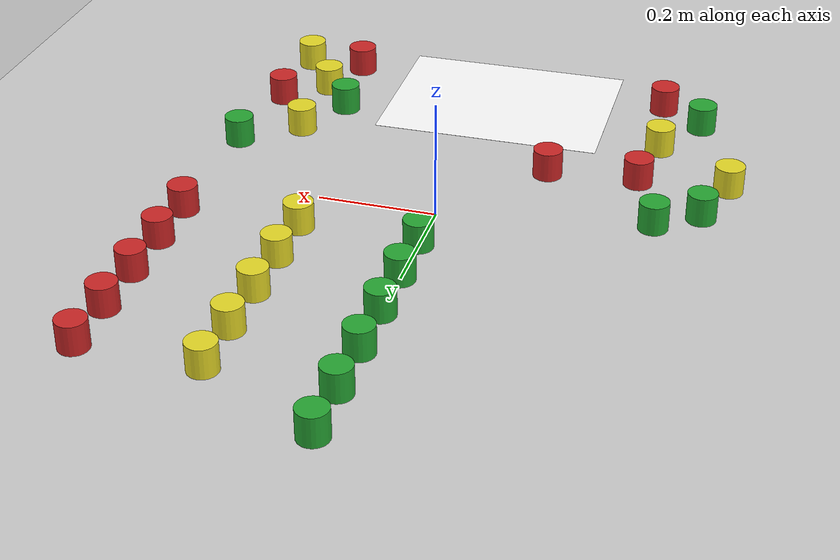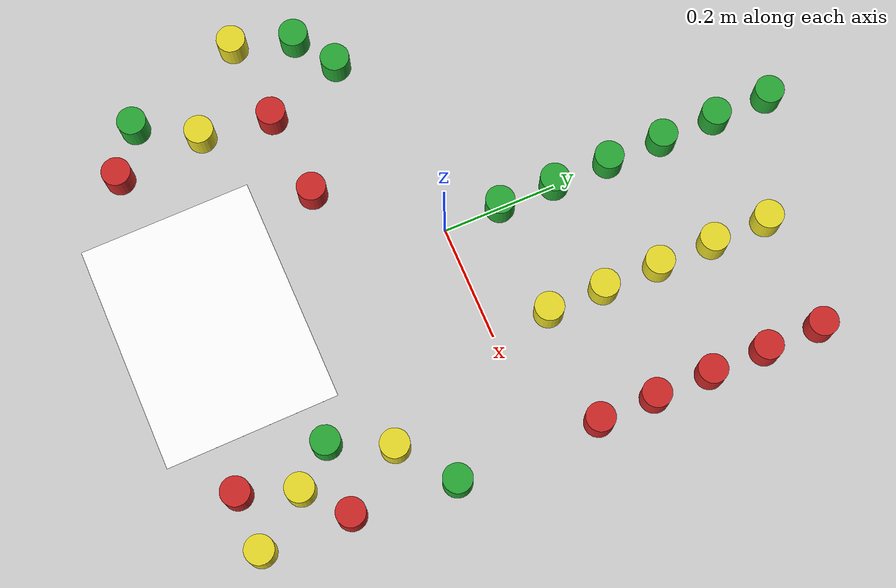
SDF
<sdf version="1.6">
 <world name="default">
  <physics type="ode">
   <ode><solver><type>quick</type></solver></ode>
   <max_step_size>0.000002</max_step_size>
   <real_time_factor>1</real_time_factor>
   <real_time_update_rate>500000</real_time_update_rate>
   <gravity>0 0 -9.8</gravity>
   <update_rate>-1</update_rate>
  </physics>
  <light name="sun" type="directional">
   <pose>0 0 10 0 -0 0</pose>
   <diffuse>0.8 0.8 0.8 1</diffuse>
   <specular>0.2 0.2 0.2 1</specular>
   <attenuation>
    <range>1000</range>
    <constant>0.9</constant>
    <linear>0.01</linear>
    <quadratic>0.001</quadratic>
   </attenuation>
   <direction>-0.5 0.1 -0.9</direction>
  </light>
  <model name="ground_plane">
   <static>1</static>
   <link name="link">
    <collision name="collision">
     <geometry><plane><normal>0 0 1</normal><size>100 100</size></plane></geometry>
     <surface>
      <contact><collide_bitmask>65535</collide_bitmask></contact>
      <friction><ode><mu>100</mu><mu2>50</mu2></ode></friction>
     </surface>
    </collision>
    <visual name="visual">
     <cast_shadows>0</cast_shadows>
     <geometry><plane><normal>0 0 1</normal><size>100 100</size></plane></geometry>
     <material>
      <script><uri>file://media/materials/scripts/gazebo.material</uri><name>Gazebo/Grey</name></script>
     </material>
    </visual>
   </link>
  </model>
  <gravity>0 0 -9.8</gravity>
  <magnetic_field>6e-06 2.3e-05 -4.2e-05</magnetic_field>
  <atmosphere type="adiabatic"/>
  <physics name="default_physics" default="0" type="ode">
   <max_step_size>0.001</max_step_size>
   <real_time_factor>1</real_time_factor>
   <real_time_update_rate>1000</real_time_update_rate>
  </physics>
  <scene><ambient>0.4 0.4 0.4 1</ambient><background>0.7 0.7 0.7 1</background><shadows>1</shadows></scene>
  <spherical_coordinates>
   <surface_model>EARTH_WGS84</surface_model>
   <latitude_deg>0</latitude_deg>
   <longitude_deg>0</longitude_deg>
   <elevation>0</elevation>
   <heading_deg>0</heading_deg>
  </spherical_coordinates>
  <model name="traffic_lights_board">
   <link name="link">
    <inertial>
     <mass>1</mass>
     <inertia><ixx>1</ixx><ixy>0</ixy><ixz>0</ixz><iyy>1</iyy><iyz>0</iyz><izz>1</izz></inertia>
    </inertial>
    <visual name="visual">
     <geometry><box><size>0.3 0.4 0.0001</size></box></geometry>
     <material>
      <script>
       <uri>model://traffic_lights_board/materials/scripts</uri>
       <uri>model://traffic_lights_board/materials/textures</uri>
       <name>Grid43</name>
      </script>
      <shader type="pixel"><normal_map>__default__</normal_map></shader>
      <ambient>1 1 1 1</ambient>
      <diffuse>1 1 1 1</diffuse>
      <specular>0 0 0 1</specular>
      <emissive>0 0 0 1</emissive>
     </material>
    </visual>
    <collision name="collision">
     <geometry><box><size>0.3 0.4 0.0003</size></box></geometry>
     <surface>
      <friction>
       <ode><mu>1</mu><mu2>1</mu2><fdir1>0 0 0</fdir1><slip1>0</slip1><slip2>0</slip2></ode>
       <torsional>
        <coefficient>1</coefficient>
        <patch_radius>0</patch_radius>
        <surface_radius>0</surface_radius>
        <use_patch_radius>1</use_patch_radius>
        <ode><slip>0</slip></ode>
       </torsional>
      </friction>
      <bounce><restitution_coefficient>0</restitution_coefficient><threshold>1e+06</threshold></bounce>
      <contact>
       <collide_without_contact>0</collide_without_contact>
       <collide_without_contact_bitmask>1</collide_without_contact_bitmask>
       <collide_bitmask>1</collide_bitmask>
       <ode>
        <soft_cfm>0</soft_cfm>
        <soft_erp>0.2</soft_erp>
        <kp>1e+13</kp>
        <kd>1</kd>
        <max_vel>0.01</max_vel>
        <min_depth>0</min_depth>
       </ode>
       <bullet>
        <split_impulse>1</split_impulse>
        <split_impulse_penetration_threshold>-0.01</split_impulse_penetration_threshold>
        <soft_cfm>0</soft_cfm>
        <soft_erp>0.2</soft_erp>
        <kp>1e+13</kp>
        <kd>1</kd>
       </bullet>
      </contact>
     </surface>
    </collision>
   </link>
   <static>1</static>
   <pose>-0.008431 -0.425021 0 0 0 -1.56</pose>
  </model>
  <model name="green_cylinder_short">
   <link name="blue_cylinder_link">
    <inertial>
     <mass>1</mass>
     <inertia><ixx>0.145833</ixx><ixy>0</ixy><ixz>0</ixz><iyy>0.145833</iyy><iyz>0</iyz><izz>0.125</izz></inertia>
    </inertial>
    <pose>-0 -0 0.025 0 -0 0</pose>
    <visual name="visual">
     <geometry><cylinder><radius>0.025</radius><length>0.05</length></cylinder></geometry>
     <material>
      <script><name>Gazebo/Green</name><uri>file://media/materials/scripts/gazebo.material</uri></script>
      <shader type="pixel"><normal_map>__default__</normal_map></shader>
      <ambient>0 1 0 1</ambient>
      <diffuse>0 1 0 1</diffuse>
      <specular>0 1 0 1</specular>
      <emissive>0 1 0 1</emissive>
     </material>
    </visual>
    <collision name="collision">
     <geometry><cylinder><radius>0.025</radius><length>0.05</length></cylinder></geometry>
     <surface>
      <friction>
       <ode><mu>1</mu><mu2>1</mu2><fdir1>0 0 0</fdir1><slip1>0</slip1><slip2>0</slip2></ode>
       <torsional>
        <coefficient>1</coefficient>
        <patch_radius>0</patch_radius>
        <surface_radius>0</surface_radius>
        <use_patch_radius>1</use_patch_radius>
        <ode><slip>0</slip></ode>
       </torsional>
      </friction>
      <bounce><restitution_coefficient>0</restitution_coefficient><threshold>1e+06</threshold></bounce>
      <contact>
       <collide_without_contact>0</collide_without_contact>
       <collide_without_contact_bitmask>1</collide_without_contact_bitmask>
       <collide_bitmask>1</collide_bitmask>
       <ode>
        <soft_cfm>0</soft_cfm>
        <soft_erp>0.2</soft_erp>
        <kp>1e+13</kp>
        <kd>1</kd>
        <max_vel>0.01</max_vel>
        <min_depth>0</min_depth>
       </ode>
       <bullet>
        <split_impulse>1</split_impulse>
        <split_impulse_penetration_threshold>-0.01</split_impulse_penetration_threshold>
        <soft_cfm>0</soft_cfm>
        <soft_erp>0.2</soft_erp>
        <kp>1e+13</kp>
        <kd>1</kd>
       </bullet>
      </contact>
     </surface>
    </collision>
   </link>
   <static>0</static>
   <pose>-0.347585 -0.056651 0 0 -0 0</pose>
  </model>
  <model name="green_cylinder_short_clone">
   <link name="blue_cylinder_link">
    <inertial>
     <mass>1</mass>
     <inertia><ixx>0.145833</ixx><ixy>0</ixy><ixz>0</ixz><iyy>0.145833</iyy><iyz>0</iyz><izz>0.125</izz></inertia>
    </inertial>
    <pose>-0 -0 0.025 0 -0 0</pose>
    <visual name="visual">
     <geometry><cylinder><radius>0.025</radius><length>0.05</length></cylinder></geometry>
     <material>
      <script><name>Gazebo/Green</name><uri>file://media/materials/scripts/gazebo.material</uri></script>
      <shader type="pixel"><normal_map>__default__</normal_map></shader>
      <ambient>0 1 0 1</ambient>
      <diffuse>0 1 0 1</diffuse>
      <specular>0 1 0 1</specular>
      <emissive>0 1 0 1</emissive>
     </material>
    </visual>
    <collision name="collision">
     <geometry><cylinder><radius>0.025</radius><length>0.05</length></cylinder></geometry>
     <surface>
      <friction>
       <ode><mu>1</mu><mu2>1</mu2><fdir1>0 0 0</fdir1><slip1>0</slip1><slip2>0</slip2></ode>
       <torsional>
        <coefficient>1</coefficient>
        <patch_radius>0</patch_radius>
        <surface_radius>0</surface_radius>
        <use_patch_radius>1</use_patch_radius>
        <ode><slip>0</slip></ode>
       </torsional>
      </friction>
      <bounce><restitution_coefficient>0</restitution_coefficient><threshold>1e+06</threshold></bounce>
      <contact>
       <collide_without_contact>0</collide_without_contact>
       <collide_without_contact_bitmask>1</collide_without_contact_bitmask>
       <collide_bitmask>1</collide_bitmask>
       <ode>
        <soft_cfm>0</soft_cfm>
        <soft_erp>0.2</soft_erp>
        <kp>1e+13</kp>
        <kd>1</kd>
        <max_vel>0.01</max_vel>
        <min_depth>0</min_depth>
       </ode>
       <bullet>
        <split_impulse>1</split_impulse>
        <split_impulse_penetration_threshold>-0.01</split_impulse_penetration_threshold>
        <soft_cfm>0</soft_cfm>
        <soft_erp>0.2</soft_erp>
        <kp>1e+13</kp>
        <kd>1</kd>
       </bullet>
      </contact>
     </surface>
    </collision>
   </link>
   <static>0</static>
   <pose>-0.418127 -0.105245 0 -1e-06 1e-06 -1e-06</pose>
  </model>
  <model name="green_cylinder_short_clone_0">
   <link name="blue_cylinder_link">
    <inertial>
     <mass>1</mass>
     <inertia><ixx>0.145833</ixx><ixy>0</ixy><ixz>0</ixz><iyy>0.145833</iyy><iyz>0</iyz><izz>0.125</izz></inertia>
    </inertial>
    <pose>-0 -0 0.025 0 -0 0</pose>
    <visual name="visual">
     <geometry><cylinder><radius>0.025</radius><length>0.05</length></cylinder></geometry>
     <material>
      <script><name>Gazebo/Green</name><uri>file://media/materials/scripts/gazebo.material</uri></script>
      <shader type="pixel"><normal_map>__default__</normal_map></shader>
      <ambient>0 1 0 1</ambient>
      <diffuse>0 1 0 1</diffuse>
      <specular>0 1 0 1</specular>
      <emissive>0 1 0 1</emissive>
     </material>
    </visual>
    <collision name="collision">
     <geometry><cylinder><radius>0.025</radius><length>0.05</length></cylinder></geometry>
     <surface>
      <friction>
       <ode><mu>1</mu><mu2>1</mu2><fdir1>0 0 0</fdir1><slip1>0</slip1><slip2>0</slip2></ode>
       <torsional>
        <coefficient>1</coefficient>
        <patch_radius>0</patch_radius>
        <surface_radius>0</surface_radius>
        <use_patch_radius>1</use_patch_radius>
        <ode><slip>0</slip></ode>
       </torsional>
      </friction>
      <bounce><restitution_coefficient>0</restitution_coefficient><threshold>1e+06</threshold></bounce>
      <contact>
       <collide_without_contact>0</collide_without_contact>
       <collide_without_contact_bitmask>1</collide_without_contact_bitmask>
       <collide_bitmask>1</collide_bitmask>
       <ode>
        <soft_cfm>0</soft_cfm>
        <soft_erp>0.2</soft_erp>
        <kp>1e+13</kp>
        <kd>1</kd>
        <max_vel>0.01</max_vel>
        <min_depth>0</min_depth>
       </ode>
       <bullet>
        <split_impulse>1</split_impulse>
        <split_impulse_penetration_threshold>-0.01</split_impulse_penetration_threshold>
        <soft_cfm>0</soft_cfm>
        <soft_erp>0.2</soft_erp>
        <kp>1e+13</kp>
        <kd>1</kd>
       </bullet>
      </contact>
     </surface>
    </collision>
   </link>
   <static>0</static>
   <pose>0.4 -0.149757 0 -1e-06 1e-06 -1e-06</pose>
  </model>
  <model name="green_cylinder_short_clone_1">
   <link name="blue_cylinder_link">
    <inertial>
     <mass>1</mass>
     <inertia><ixx>0.145833</ixx><ixy>0</ixy><ixz>0</ixz><iyy>0.145833</iyy><iyz>0</iyz><izz>0.125</izz></inertia>
    </inertial>
    <pose>-0 -0 0.025 0 -0 0</pose>
    <visual name="visual">
     <geometry><cylinder><radius>0.025</radius><length>0.05</length></cylinder></geometry>
     <material>
      <script><name>Gazebo/Green</name><uri>file://media/materials/scripts/gazebo.material</uri></script>
      <shader type="pixel"><normal_map>__default__</normal_map></shader>
      <ambient>0 1 0 1</ambient>
      <diffuse>0 1 0 1</diffuse>
      <specular>0 1 0 1</specular>
      <emissive>0 1 0 1</emissive>
     </material>
    </visual>
    <collision name="collision">
     <geometry><cylinder><radius>0.025</radius><length>0.05</length></cylinder></geometry>
     <surface>
      <friction>
       <ode><mu>1</mu><mu2>1</mu2><fdir1>0 0 0</fdir1><slip1>0</slip1><slip2>0</slip2></ode>
       <torsional>
        <coefficient>1</coefficient>
        <patch_radius>0</patch_radius>
        <surface_radius>0</surface_radius>
        <use_patch_radius>1</use_patch_radius>
        <ode><slip>0</slip></ode>
       </torsional>
      </friction>
      <bounce><restitution_coefficient>0</restitution_coefficient><threshold>1e+06</threshold></bounce>
      <contact>
       <collide_without_contact>0</collide_without_contact>
       <collide_without_contact_bitmask>1</collide_without_contact_bitmask>
       <collide_bitmask>1</collide_bitmask>
       <ode>
        <soft_cfm>0</soft_cfm>
        <soft_erp>0.2</soft_erp>
        <kp>1e+13</kp>
        <kd>1</kd>
        <max_vel>0.01</max_vel>
        <min_depth>0</min_depth>
       </ode>
       <bullet>
        <split_impulse>1</split_impulse>
        <split_impulse_penetration_threshold>-0.01</split_impulse_penetration_threshold>
        <soft_cfm>0</soft_cfm>
        <soft_erp>0.2</soft_erp>
        <kp>1e+13</kp>
        <kd>1</kd>
       </bullet>
      </contact>
     </surface>
    </collision>
   </link>
   <static>0</static>
   <pose>-0.375425 -0.415999 0 -1e-06 1e-06 -1e-06</pose>
  </model>
  <model name="green_cylinder_short_clone_2">
   <link name="blue_cylinder_link">
    <inertial>
     <mass>1</mass>
     <inertia><ixx>0.145833</ixx><ixy>0</ixy><ixz>0</ixz><iyy>0.145833</iyy><iyz>0</iyz><izz>0.125</izz></inertia>
    </inertial>
    <pose>-0 -0 0.025 0 -0 0</pose>
    <visual name="visual">
     <geometry><cylinder><radius>0.025</radius><length>0.05</length></cylinder></geometry>
     <material>
      <script><name>Gazebo/Green</name><uri>file://media/materials/scripts/gazebo.material</uri></script>
      <shader type="pixel"><normal_map>__default__</normal_map></shader>
      <ambient>0 1 0 1</ambient>
      <diffuse>0 1 0 1</diffuse>
      <specular>0 1 0 1</specular>
      <emissive>0 1 0 1</emissive>
     </material>
    </visual>
    <collision name="collision">
     <geometry><cylinder><radius>0.025</radius><length>0.05</length></cylinder></geometry>
     <surface>
      <friction>
       <ode><mu>1</mu><mu2>1</mu2><fdir1>0 0 0</fdir1><slip1>0</slip1><slip2>0</slip2></ode>
       <torsional>
        <coefficient>1</coefficient>
        <patch_radius>0</patch_radius>
        <surface_radius>0</surface_radius>
        <use_patch_radius>1</use_patch_radius>
        <ode><slip>0</slip></ode>
       </torsional>
      </friction>
      <bounce><restitution_coefficient>0</restitution_coefficient><threshold>1e+06</threshold></bounce>
      <contact>
       <collide_without_contact>0</collide_without_contact>
       <collide_without_contact_bitmask>1</collide_without_contact_bitmask>
       <collide_bitmask>1</collide_bitmask>
       <ode>
        <soft_cfm>0</soft_cfm>
        <soft_erp>0.2</soft_erp>
        <kp>1e+13</kp>
        <kd>1</kd>
        <max_vel>0.01</max_vel>
        <min_depth>0</min_depth>
       </ode>
       <bullet>
        <split_impulse>1</split_impulse>
        <split_impulse_penetration_threshold>-0.01</split_impulse_penetration_threshold>
        <soft_cfm>0</soft_cfm>
        <soft_erp>0.2</soft_erp>
        <kp>1e+13</kp>
        <kd>1</kd>
       </bullet>
      </contact>
     </surface>
    </collision>
   </link>
   <static>0</static>
   <pose>0.26 -0.32 0 -1e-06 1e-06 -1e-06</pose>
  </model>
  <model name="green_cylinder_short_clone_3">
   <link name="blue_cylinder_link">
    <inertial>
     <mass>1</mass>
     <inertia><ixx>0.145833</ixx><ixy>0</ixy><ixz>0</ixz><iyy>0.145833</iyy><iyz>0</iyz><izz>0.125</izz></inertia>
    </inertial>
    <pose>-0 -0 0.025 0 -0 0</pose>
    <visual name="visual">
     <geometry><cylinder><radius>0.025</radius><length>0.05</length></cylinder></geometry>
     <material>
      <script><name>Gazebo/Green</name><uri>file://media/materials/scripts/gazebo.material</uri></script>
      <shader type="pixel"><normal_map>__default__</normal_map></shader>
      <ambient>0 1 0 1</ambient>
      <diffuse>0 1 0 1</diffuse>
      <specular>0 1 0 1</specular>
      <emissive>0 1 0 1</emissive>
     </material>
    </visual>
    <collision name="collision">
     <geometry><cylinder><radius>0.025</radius><length>0.05</length></cylinder></geometry>
     <surface>
      <friction>
       <ode><mu>1</mu><mu2>1</mu2><fdir1>0 0 0</fdir1><slip1>0</slip1><slip2>0</slip2></ode>
       <torsional>
        <coefficient>1</coefficient>
        <patch_radius>0</patch_radius>
        <surface_radius>0</surface_radius>
        <use_patch_radius>1</use_patch_radius>
        <ode><slip>0</slip></ode>
       </torsional>
      </friction>
      <bounce><restitution_coefficient>0</restitution_coefficient><threshold>1e+06</threshold></bounce>
      <contact>
       <collide_without_contact>0</collide_without_contact>
       <collide_without_contact_bitmask>1</collide_without_contact_bitmask>
       <collide_bitmask>1</collide_bitmask>
       <ode>
        <soft_cfm>0</soft_cfm>
        <soft_erp>0.2</soft_erp>
        <kp>1e+13</kp>
        <kd>1</kd>
        <max_vel>0.01</max_vel>
        <min_depth>0</min_depth>
       </ode>
       <bullet>
        <split_impulse>1</split_impulse>
        <split_impulse_penetration_threshold>-0.01</split_impulse_penetration_threshold>
        <soft_cfm>0</soft_cfm>
        <soft_erp>0.2</soft_erp>
        <kp>1e+13</kp>
        <kd>1</kd>
       </bullet>
      </contact>
     </surface>
    </collision>
   </link>
   <static>0</static>
   <pose>0 0.1 0 -1e-06 1e-06 -1e-06</pose>
  </model>
  <model name="green_cylinder_short_clone_4">
   <link name="blue_cylinder_link">
    <inertial>
     <mass>1</mass>
     <inertia><ixx>0.145833</ixx><ixy>0</ixy><ixz>0</ixz><iyy>0.145833</iyy><iyz>0</iyz><izz>0.125</izz></inertia>
    </inertial>
    <pose>-0 -0 0.025 0 -0 0</pose>
    <visual name="visual">
     <geometry><cylinder><radius>0.025</radius><length>0.05</length></cylinder></geometry>
     <material>
      <script><name>Gazebo/Green</name><uri>file://media/materials/scripts/gazebo.material</uri></script>
      <shader type="pixel"><normal_map>__default__</normal_map></shader>
      <ambient>0 1 0 1</ambient>
      <diffuse>0 1 0 1</diffuse>
      <specular>0 1 0 1</specular>
      <emissive>0 1 0 1</emissive>
     </material>
    </visual>
    <collision name="collision">
     <geometry><cylinder><radius>0.025</radius><length>0.05</length></cylinder></geometry>
     <surface>
      <friction>
       <ode><mu>1</mu><mu2>1</mu2><fdir1>0 0 0</fdir1><slip1>0</slip1><slip2>0</slip2></ode>
       <torsional>
        <coefficient>1</coefficient>
        <patch_radius>0</patch_radius>
        <surface_radius>0</surface_radius>
        <use_patch_radius>1</use_patch_radius>
        <ode><slip>0</slip></ode>
       </torsional>
      </friction>
      <bounce><restitution_coefficient>0</restitution_coefficient><threshold>1e+06</threshold></bounce>
      <contact>
       <collide_without_contact>0</collide_without_contact>
       <collide_without_contact_bitmask>1</collide_without_contact_bitmask>
       <collide_bitmask>1</collide_bitmask>
       <ode>
        <soft_cfm>0</soft_cfm>
        <soft_erp>0.2</soft_erp>
        <kp>1e+13</kp>
        <kd>1</kd>
        <max_vel>0.01</max_vel>
        <min_depth>0</min_depth>
       </ode>
       <bullet>
        <split_impulse>1</split_impulse>
        <split_impulse_penetration_threshold>-0.01</split_impulse_penetration_threshold>
        <soft_cfm>0</soft_cfm>
        <soft_erp>0.2</soft_erp>
        <kp>1e+13</kp>
        <kd>1</kd>
       </bullet>
      </contact>
     </surface>
    </collision>
   </link>
   <static>0</static>
   <pose>0 0.2 0 -1e-06 1e-06 -1e-06</pose>
  </model>
  <model name="green_cylinder_short_clone_5">
   <link name="blue_cylinder_link">
    <inertial>
     <mass>1</mass>
     <inertia><ixx>0.145833</ixx><ixy>0</ixy><ixz>0</ixz><iyy>0.145833</iyy><iyz>0</iyz><izz>0.125</izz></inertia>
    </inertial>
    <pose>-0 -0 0.025 0 -0 0</pose>
    <visual name="visual">
     <geometry><cylinder><radius>0.025</radius><length>0.05</length></cylinder></geometry>
     <material>
      <script><name>Gazebo/Green</name><uri>file://media/materials/scripts/gazebo.material</uri></script>
      <shader type="pixel"><normal_map>__default__</normal_map></shader>
      <ambient>0 1 0 1</ambient>
      <diffuse>0 1 0 1</diffuse>
      <specular>0 1 0 1</specular>
      <emissive>0 1 0 1</emissive>
     </material>
    </visual>
    <collision name="collision">
     <geometry><cylinder><radius>0.025</radius><length>0.05</length></cylinder></geometry>
     <surface>
      <friction>
       <ode><mu>1</mu><mu2>1</mu2><fdir1>0 0 0</fdir1><slip1>0</slip1><slip2>0</slip2></ode>
       <torsional>
        <coefficient>1</coefficient>
        <patch_radius>0</patch_radius>
        <surface_radius>0</surface_radius>
        <use_patch_radius>1</use_patch_radius>
        <ode><slip>0</slip></ode>
       </torsional>
      </friction>
      <bounce><restitution_coefficient>0</restitution_coefficient><threshold>1e+06</threshold></bounce>
      <contact>
       <collide_without_contact>0</collide_without_contact>
       <collide_without_contact_bitmask>1</collide_without_contact_bitmask>
       <collide_bitmask>1</collide_bitmask>
       <ode>
        <soft_cfm>0</soft_cfm>
        <soft_erp>0.2</soft_erp>
        <kp>1e+13</kp>
        <kd>1</kd>
        <max_vel>0.01</max_vel>
        <min_depth>0</min_depth>
       </ode>
       <bullet>
        <split_impulse>1</split_impulse>
        <split_impulse_penetration_threshold>-0.01</split_impulse_penetration_threshold>
        <soft_cfm>0</soft_cfm>
        <soft_erp>0.2</soft_erp>
        <kp>1e+13</kp>
        <kd>1</kd>
       </bullet>
      </contact>
     </surface>
    </collision>
   </link>
   <static>0</static>
   <pose>0 0.3 0 -1e-06 1e-06 -1e-06</pose>
  </model>
  <model name="green_cylinder_short_clone_6">
   <link name="blue_cylinder_link">
    <inertial>
     <mass>1</mass>
     <inertia><ixx>0.145833</ixx><ixy>0</ixy><ixz>0</ixz><iyy>0.145833</iyy><iyz>0</iyz><izz>0.125</izz></inertia>
    </inertial>
    <pose>-0 -0 0.025 0 -0 0</pose>
    <visual name="visual">
     <geometry><cylinder><radius>0.025</radius><length>0.05</length></cylinder></geometry>
     <material>
      <script><name>Gazebo/Green</name><uri>file://media/materials/scripts/gazebo.material</uri></script>
      <shader type="pixel"><normal_map>__default__</normal_map></shader>
      <ambient>0 1 0 1</ambient>
      <diffuse>0 1 0 1</diffuse>
      <specular>0 1 0 1</specular>
      <emissive>0 1 0 1</emissive>
     </material>
    </visual>
    <collision name="collision">
     <geometry><cylinder><radius>0.025</radius><length>0.05</length></cylinder></geometry>
     <surface>
      <friction>
       <ode><mu>1</mu><mu2>1</mu2><fdir1>0 0 0</fdir1><slip1>0</slip1><slip2>0</slip2></ode>
       <torsional>
        <coefficient>1</coefficient>
        <patch_radius>0</patch_radius>
        <surface_radius>0</surface_radius>
        <use_patch_radius>1</use_patch_radius>
        <ode><slip>0</slip></ode>
       </torsional>
      </friction>
      <bounce><restitution_coefficient>0</restitution_coefficient><threshold>1e+06</threshold></bounce>
      <contact>
       <collide_without_contact>0</collide_without_contact>
       <collide_without_contact_bitmask>1</collide_without_contact_bitmask>
       <collide_bitmask>1</collide_bitmask>
       <ode>
        <soft_cfm>0</soft_cfm>
        <soft_erp>0.2</soft_erp>
        <kp>1e+13</kp>
        <kd>1</kd>
        <max_vel>0.01</max_vel>
        <min_depth>0</min_depth>
       </ode>
       <bullet>
        <split_impulse>1</split_impulse>
        <split_impulse_penetration_threshold>-0.01</split_impulse_penetration_threshold>
        <soft_cfm>0</soft_cfm>
        <soft_erp>0.2</soft_erp>
        <kp>1e+13</kp>
        <kd>1</kd>
       </bullet>
      </contact>
     </surface>
    </collision>
   </link>
   <static>0</static>
   <pose>0 0.4 0 -1e-06 1e-06 -1e-06</pose>
  </model>
  <model name="green_cylinder_short_clone_7">
   <link name="blue_cylinder_link">
    <inertial>
     <mass>1</mass>
     <inertia><ixx>0.145833</ixx><ixy>0</ixy><ixz>0</ixz><iyy>0.145833</iyy><iyz>0</iyz><izz>0.125</izz></inertia>
    </inertial>
    <pose>-0 -0 0.025 0 -0 0</pose>
    <visual name="visual">
     <geometry><cylinder><radius>0.025</radius><length>0.05</length></cylinder></geometry>
     <material>
      <script><name>Gazebo/Green</name><uri>file://media/materials/scripts/gazebo.material</uri></script>
      <shader type="pixel"><normal_map>__default__</normal_map></shader>
      <ambient>0 1 0 1</ambient>
      <diffuse>0 1 0 1</diffuse>
      <specular>0 1 0 1</specular>
      <emissive>0 1 0 1</emissive>
     </material>
    </visual>
    <collision name="collision">
     <geometry><cylinder><radius>0.025</radius><length>0.05</length></cylinder></geometry>
     <surface>
      <friction>
       <ode><mu>1</mu><mu2>1</mu2><fdir1>0 0 0</fdir1><slip1>0</slip1><slip2>0</slip2></ode>
       <torsional>
        <coefficient>1</coefficient>
        <patch_radius>0</patch_radius>
        <surface_radius>0</surface_radius>
        <use_patch_radius>1</use_patch_radius>
        <ode><slip>0</slip></ode>
       </torsional>
      </friction>
      <bounce><restitution_coefficient>0</restitution_coefficient><threshold>1e+06</threshold></bounce>
      <contact>
       <collide_without_contact>0</collide_without_contact>
       <collide_without_contact_bitmask>1</collide_without_contact_bitmask>
       <collide_bitmask>1</collide_bitmask>
       <ode>
        <soft_cfm>0</soft_cfm>
        <soft_erp>0.2</soft_erp>
        <kp>1e+13</kp>
        <kd>1</kd>
        <max_vel>0.01</max_vel>
        <min_depth>0</min_depth>
       </ode>
       <bullet>
        <split_impulse>1</split_impulse>
        <split_impulse_penetration_threshold>-0.01</split_impulse_penetration_threshold>
        <soft_cfm>0</soft_cfm>
        <soft_erp>0.2</soft_erp>
        <kp>1e+13</kp>
        <kd>1</kd>
       </bullet>
      </contact>
     </surface>
    </collision>
   </link>
   <static>0</static>
   <pose>0 0.5 0 -1e-06 1e-06 -1e-06</pose>
  </model>
  <model name="green_cylinder_short_clone_8">
   <link name="blue_cylinder_link">
    <inertial>
     <mass>1</mass>
     <inertia><ixx>0.145833</ixx><ixy>0</ixy><ixz>0</ixz><iyy>0.145833</iyy><iyz>0</iyz><izz>0.125</izz></inertia>
    </inertial>
    <pose>-0 -0 0.025 0 -0 0</pose>
    <visual name="visual">
     <geometry><cylinder><radius>0.025</radius><length>0.05</length></cylinder></geometry>
     <material>
      <script><name>Gazebo/Green</name><uri>file://media/materials/scripts/gazebo.material</uri></script>
      <shader type="pixel"><normal_map>__default__</normal_map></shader>
      <ambient>0 1 0 1</ambient>
      <diffuse>0 1 0 1</diffuse>
      <specular>0 1 0 1</specular>
      <emissive>0 1 0 1</emissive>
     </material>
    </visual>
    <collision name="collision">
     <geometry><cylinder><radius>0.025</radius><length>0.05</length></cylinder></geometry>
     <surface>
      <friction>
       <ode><mu>1</mu><mu2>1</mu2><fdir1>0 0 0</fdir1><slip1>0</slip1><slip2>0</slip2></ode>
       <torsional>
        <coefficient>1</coefficient>
        <patch_radius>0</patch_radius>
        <surface_radius>0</surface_radius>
        <use_patch_radius>1</use_patch_radius>
        <ode><slip>0</slip></ode>
       </torsional>
      </friction>
      <bounce><restitution_coefficient>0</restitution_coefficient><threshold>1e+06</threshold></bounce>
      <contact>
       <collide_without_contact>0</collide_without_contact>
       <collide_without_contact_bitmask>1</collide_without_contact_bitmask>
       <collide_bitmask>1</collide_bitmask>
       <ode>
        <soft_cfm>0</soft_cfm>
        <soft_erp>0.2</soft_erp>
        <kp>1e+13</kp>
        <kd>1</kd>
        <max_vel>0.01</max_vel>
        <min_depth>0</min_depth>
       </ode>
       <bullet>
        <split_impulse>1</split_impulse>
        <split_impulse_penetration_threshold>-0.01</split_impulse_penetration_threshold>
        <soft_cfm>0</soft_cfm>
        <soft_erp>0.2</soft_erp>
        <kp>1e+13</kp>
        <kd>1</kd>
       </bullet>
      </contact>
     </surface>
    </collision>
   </link>
   <static>0</static>
   <pose>0 0.6 0 -1e-06 1e-06 -1e-06</pose>
  </model>
  <model name="yellow_cylinder_short">
   <link name="blue_cylinder_link">
    <inertial>
     <mass>1</mass>
     <inertia><ixx>0.145833</ixx><ixy>0</ixy><ixz>0</ixz><iyy>0.145833</iyy><iyz>0</iyz><izz>0.125</izz></inertia>
    </inertial>
    <pose>-0 -0 0.025 0 -0 0</pose>
    <visual name="visual">
     <geometry><cylinder><radius>0.025</radius><length>0.05</length></cylinder></geometry>
     <material>
      <script><name>Gazebo/Yellow</name><uri>file://media/materials/scripts/gazebo.material</uri></script>
      <shader type="pixel"><normal_map>__default__</normal_map></shader>
      <ambient>1 0.8 0 1</ambient>
      <diffuse>1 0.8 0 1</diffuse>
      <specular>1 0.8 0 1</specular>
      <emissive>1 0.8 0 1</emissive>
     </material>
    </visual>
    <collision name="collision">
     <geometry><cylinder><radius>0.025</radius><length>0.05</length></cylinder></geometry>
     <surface>
      <friction>
       <ode><mu>1</mu><mu2>1</mu2><fdir1>0 0 0</fdir1><slip1>0</slip1><slip2>0</slip2></ode>
       <torsional>
        <coefficient>1</coefficient>
        <patch_radius>0</patch_radius>
        <surface_radius>0</surface_radius>
        <use_patch_radius>1</use_patch_radius>
        <ode><slip>0</slip></ode>
       </torsional>
      </friction>
      <bounce><restitution_coefficient>0</restitution_coefficient><threshold>1e+06</threshold></bounce>
      <contact>
       <collide_without_contact>0</collide_without_contact>
       <collide_without_contact_bitmask>1</collide_without_contact_bitmask>
       <collide_bitmask>1</collide_bitmask>
       <ode>
        <soft_cfm>0</soft_cfm>
        <soft_erp>0.2</soft_erp>
        <kp>1e+13</kp>
        <kd>1</kd>
        <max_vel>0.01</max_vel>
        <min_depth>0</min_depth>
       </ode>
       <bullet>
        <split_impulse>1</split_impulse>
        <split_impulse_penetration_threshold>-0.01</split_impulse_penetration_threshold>
        <soft_cfm>0</soft_cfm>
        <soft_erp>0.2</soft_erp>
        <kp>1e+13</kp>
        <kd>1</kd>
       </bullet>
      </contact>
     </surface>
    </collision>
   </link>
   <static>0</static>
   <pose>-0.44932 -0.207694 0 0 -0 0</pose>
  </model>
  <model name="yellow_cylinder_short_clone">
   <link name="blue_cylinder_link">
    <inertial>
     <mass>1</mass>
     <inertia><ixx>0.145833</ixx><ixy>0</ixy><ixz>0</ixz><iyy>0.145833</iyy><iyz>0</iyz><izz>0.125</izz></inertia>
    </inertial>
    <pose>-0 -0 0.025 0 -0 0</pose>
    <visual name="visual">
     <geometry><cylinder><radius>0.025</radius><length>0.05</length></cylinder></geometry>
     <material>
      <script><name>Gazebo/Yellow</name><uri>file://media/materials/scripts/gazebo.material</uri></script>
      <shader type="pixel"><normal_map>__default__</normal_map></shader>
      <ambient>1 0.8 0 1</ambient>
      <diffuse>1 0.8 0 1</diffuse>
      <specular>1 0.8 0 1</specular>
      <emissive>1 0.8 0 1</emissive>
     </material>
    </visual>
    <collision name="collision">
     <geometry><cylinder><radius>0.025</radius><length>0.05</length></cylinder></geometry>
     <surface>
      <friction>
       <ode><mu>1</mu><mu2>1</mu2><fdir1>0 0 0</fdir1><slip1>0</slip1><slip2>0</slip2></ode>
       <torsional>
        <coefficient>1</coefficient>
        <patch_radius>0</patch_radius>
        <surface_radius>0</surface_radius>
        <use_patch_radius>1</use_patch_radius>
        <ode><slip>0</slip></ode>
       </torsional>
      </friction>
      <bounce><restitution_coefficient>0</restitution_coefficient><threshold>1e+06</threshold></bounce>
      <contact>
       <collide_without_contact>0</collide_without_contact>
       <collide_without_contact_bitmask>1</collide_without_contact_bitmask>
       <collide_bitmask>1</collide_bitmask>
       <ode>
        <soft_cfm>0</soft_cfm>
        <soft_erp>0.2</soft_erp>
        <kp>1e+13</kp>
        <kd>1</kd>
        <max_vel>0.01</max_vel>
        <min_depth>0</min_depth>
       </ode>
       <bullet>
        <split_impulse>1</split_impulse>
        <split_impulse_penetration_threshold>-0.01</split_impulse_penetration_threshold>
        <soft_cfm>0</soft_cfm>
        <soft_erp>0.2</soft_erp>
        <kp>1e+13</kp>
        <kd>1</kd>
       </bullet>
      </contact>
     </surface>
    </collision>
   </link>
   <static>0</static>
   <pose>0.308689 -0.219999 -0 -1e-06 1e-06 -1e-06</pose>
  </model>
  <model name="yellow_cylinder_short_clone_0">
   <link name="blue_cylinder_link">
    <inertial>
     <mass>1</mass>
     <inertia><ixx>0.145833</ixx><ixy>0</ixy><ixz>0</ixz><iyy>0.145833</iyy><iyz>0</iyz><izz>0.125</izz></inertia>
    </inertial>
    <pose>-0 -0 0.025 0 -0 0</pose>
    <visual name="visual">
     <geometry><cylinder><radius>0.025</radius><length>0.05</length></cylinder></geometry>
     <material>
      <script><name>Gazebo/Yellow</name><uri>file://media/materials/scripts/gazebo.material</uri></script>
      <shader type="pixel"><normal_map>__default__</normal_map></shader>
      <ambient>1 0.8 0 1</ambient>
      <diffuse>1 0.8 0 1</diffuse>
      <specular>1 0.8 0 1</specular>
      <emissive>1 0.8 0 1</emissive>
     </material>
    </visual>
    <collision name="collision">
     <geometry><cylinder><radius>0.025</radius><length>0.05</length></cylinder></geometry>
     <surface>
      <friction>
       <ode><mu>1</mu><mu2>1</mu2><fdir1>0 0 0</fdir1><slip1>0</slip1><slip2>0</slip2></ode>
       <torsional>
        <coefficient>1</coefficient>
        <patch_radius>0</patch_radius>
        <surface_radius>0</surface_radius>
        <use_patch_radius>1</use_patch_radius>
        <ode><slip>0</slip></ode>
       </torsional>
      </friction>
      <bounce><restitution_coefficient>0</restitution_coefficient><threshold>1e+06</threshold></bounce>
      <contact>
       <collide_without_contact>0</collide_without_contact>
       <collide_without_contact_bitmask>1</collide_without_contact_bitmask>
       <collide_bitmask>1</collide_bitmask>
       <ode>
        <soft_cfm>0</soft_cfm>
        <soft_erp>0.2</soft_erp>
        <kp>1e+13</kp>
        <kd>1</kd>
        <max_vel>0.01</max_vel>
        <min_depth>0</min_depth>
       </ode>
       <bullet>
        <split_impulse>1</split_impulse>
        <split_impulse_penetration_threshold>-0.01</split_impulse_penetration_threshold>
        <soft_cfm>0</soft_cfm>
        <soft_erp>0.2</soft_erp>
        <kp>1e+13</kp>
        <kd>1</kd>
       </bullet>
      </contact>
     </surface>
    </collision>
   </link>
   <static>0</static>
   <pose>0.38 -0.48 -0 -1e-06 1e-06 -1e-06</pose>
  </model>
  <model name="yellow_cylinder_short_clone_1">
   <link name="blue_cylinder_link">
    <inertial>
     <mass>1</mass>
     <inertia><ixx>0.145833</ixx><ixy>0</ixy><ixz>0</ixz><iyy>0.145833</iyy><iyz>0</iyz><izz>0.125</izz></inertia>
    </inertial>
    <pose>-0 -0 0.025 0 -0 0</pose>
    <visual name="visual">
     <geometry><cylinder><radius>0.025</radius><length>0.05</length></cylinder></geometry>
     <material>
      <script><name>Gazebo/Yellow</name><uri>file://media/materials/scripts/gazebo.material</uri></script>
      <shader type="pixel"><normal_map>__default__</normal_map></shader>
      <ambient>1 0.8 0 1</ambient>
      <diffuse>1 0.8 0 1</diffuse>
      <specular>1 0.8 0 1</specular>
      <emissive>1 0.8 0 1</emissive>
     </material>
    </visual>
    <collision name="collision">
     <geometry><cylinder><radius>0.025</radius><length>0.05</length></cylinder></geometry>
     <surface>
      <friction>
       <ode><mu>1</mu><mu2>1</mu2><fdir1>0 0 0</fdir1><slip1>0</slip1><slip2>0</slip2></ode>
       <torsional>
        <coefficient>1</coefficient>
        <patch_radius>0</patch_radius>
        <surface_radius>0</surface_radius>
        <use_patch_radius>1</use_patch_radius>
        <ode><slip>0</slip></ode>
       </torsional>
      </friction>
      <bounce><restitution_coefficient>0</restitution_coefficient><threshold>1e+06</threshold></bounce>
      <contact>
       <collide_without_contact>0</collide_without_contact>
       <collide_without_contact_bitmask>1</collide_without_contact_bitmask>
       <collide_bitmask>1</collide_bitmask>
       <ode>
        <soft_cfm>0</soft_cfm>
        <soft_erp>0.2</soft_erp>
        <kp>1e+13</kp>
        <kd>1</kd>
        <max_vel>0.01</max_vel>
        <min_depth>0</min_depth>
       </ode>
       <bullet>
        <split_impulse>1</split_impulse>
        <split_impulse_penetration_threshold>-0.01</split_impulse_penetration_threshold>
        <soft_cfm>0</soft_cfm>
        <soft_erp>0.2</soft_erp>
        <kp>1e+13</kp>
        <kd>1</kd>
       </bullet>
      </contact>
     </surface>
    </collision>
   </link>
   <static>0</static>
   <pose>0.314098 -0.385947 -0 -1e-06 1e-06 -1e-06</pose>
  </model>
  <model name="yellow_cylinder_short_clone_2">
   <link name="blue_cylinder_link">
    <inertial>
     <mass>1</mass>
     <inertia><ixx>0.145833</ixx><ixy>0</ixy><ixz>0</ixz><iyy>0.145833</iyy><iyz>0</iyz><izz>0.125</izz></inertia>
    </inertial>
    <pose>-0 -0 0.025 0 -0 0</pose>
    <visual name="visual">
     <geometry><cylinder><radius>0.025</radius><length>0.05</length></cylinder></geometry>
     <material>
      <script><name>Gazebo/Yellow</name><uri>file://media/materials/scripts/gazebo.material</uri></script>
      <shader type="pixel"><normal_map>__default__</normal_map></shader>
      <ambient>1 0.8 0 1</ambient>
      <diffuse>1 0.8 0 1</diffuse>
      <specular>1 0.8 0 1</specular>
      <emissive>1 0.8 0 1</emissive>
     </material>
    </visual>
    <collision name="collision">
     <geometry><cylinder><radius>0.025</radius><length>0.05</length></cylinder></geometry>
     <surface>
      <friction>
       <ode><mu>1</mu><mu2>1</mu2><fdir1>0 0 0</fdir1><slip1>0</slip1><slip2>0</slip2></ode>
       <torsional>
        <coefficient>1</coefficient>
        <patch_radius>0</patch_radius>
        <surface_radius>0</surface_radius>
        <use_patch_radius>1</use_patch_radius>
        <ode><slip>0</slip></ode>
       </torsional>
      </friction>
      <bounce><restitution_coefficient>0</restitution_coefficient><threshold>1e+06</threshold></bounce>
      <contact>
       <collide_without_contact>0</collide_without_contact>
       <collide_without_contact_bitmask>1</collide_without_contact_bitmask>
       <collide_bitmask>1</collide_bitmask>
       <ode>
        <soft_cfm>0</soft_cfm>
        <soft_erp>0.2</soft_erp>
        <kp>1e+13</kp>
        <kd>1</kd>
        <max_vel>0.01</max_vel>
        <min_depth>0</min_depth>
       </ode>
       <bullet>
        <split_impulse>1</split_impulse>
        <split_impulse_penetration_threshold>-0.01</split_impulse_penetration_threshold>
        <soft_cfm>0</soft_cfm>
        <soft_erp>0.2</soft_erp>
        <kp>1e+13</kp>
        <kd>1</kd>
       </bullet>
      </contact>
     </surface>
    </collision>
   </link>
   <static>0</static>
   <pose>-0.316186 -0.317194 -0 -1e-06 1e-06 -1e-06</pose>
  </model>
  <model name="yellow_cylinder_short_clone_3">
   <link name="blue_cylinder_link">
    <inertial>
     <mass>1</mass>
     <inertia><ixx>0.145833</ixx><ixy>0</ixy><ixz>0</ixz><iyy>0.145833</iyy><iyz>0</iyz><izz>0.125</izz></inertia>
    </inertial>
    <pose>-0 -0 0.025 0 -0 0</pose>
    <visual name="visual">
     <geometry><cylinder><radius>0.025</radius><length>0.05</length></cylinder></geometry>
     <material>
      <script><name>Gazebo/Yellow</name><uri>file://media/materials/scripts/gazebo.material</uri></script>
      <shader type="pixel"><normal_map>__default__</normal_map></shader>
      <ambient>1 0.8 0 1</ambient>
      <diffuse>1 0.8 0 1</diffuse>
      <specular>1 0.8 0 1</specular>
      <emissive>1 0.8 0 1</emissive>
     </material>
    </visual>
    <collision name="collision">
     <geometry><cylinder><radius>0.025</radius><length>0.05</length></cylinder></geometry>
     <surface>
      <friction>
       <ode><mu>1</mu><mu2>1</mu2><fdir1>0 0 0</fdir1><slip1>0</slip1><slip2>0</slip2></ode>
       <torsional>
        <coefficient>1</coefficient>
        <patch_radius>0</patch_radius>
        <surface_radius>0</surface_radius>
        <use_patch_radius>1</use_patch_radius>
        <ode><slip>0</slip></ode>
       </torsional>
      </friction>
      <bounce><restitution_coefficient>0</restitution_coefficient><threshold>1e+06</threshold></bounce>
      <contact>
       <collide_without_contact>0</collide_without_contact>
       <collide_without_contact_bitmask>1</collide_without_contact_bitmask>
       <collide_bitmask>1</collide_bitmask>
       <ode>
        <soft_cfm>0</soft_cfm>
        <soft_erp>0.2</soft_erp>
        <kp>1e+13</kp>
        <kd>1</kd>
        <max_vel>0.01</max_vel>
        <min_depth>0</min_depth>
       </ode>
       <bullet>
        <split_impulse>1</split_impulse>
        <split_impulse_penetration_threshold>-0.01</split_impulse_penetration_threshold>
        <soft_cfm>0</soft_cfm>
        <soft_erp>0.2</soft_erp>
        <kp>1e+13</kp>
        <kd>1</kd>
       </bullet>
      </contact>
     </surface>
    </collision>
   </link>
   <static>0</static>
   <pose>0.2 0.1 0 -1e-06 1e-06 -1e-06</pose>
  </model>
  <model name="yellow_cylinder_short_clone_4">
   <link name="blue_cylinder_link">
    <inertial>
     <mass>1</mass>
     <inertia><ixx>0.145833</ixx><ixy>0</ixy><ixz>0</ixz><iyy>0.145833</iyy><iyz>0</iyz><izz>0.125</izz></inertia>
    </inertial>
    <pose>-0 -0 0.025 0 -0 0</pose>
    <visual name="visual">
     <geometry><cylinder><radius>0.025</radius><length>0.05</length></cylinder></geometry>
     <material>
      <script><name>Gazebo/Yellow</name><uri>file://media/materials/scripts/gazebo.material</uri></script>
      <shader type="pixel"><normal_map>__default__</normal_map></shader>
      <ambient>1 0.8 0 1</ambient>
      <diffuse>1 0.8 0 1</diffuse>
      <specular>1 0.8 0 1</specular>
      <emissive>1 0.8 0 1</emissive>
     </material>
    </visual>
    <collision name="collision">
     <geometry><cylinder><radius>0.025</radius><length>0.05</length></cylinder></geometry>
     <surface>
      <friction>
       <ode><mu>1</mu><mu2>1</mu2><fdir1>0 0 0</fdir1><slip1>0</slip1><slip2>0</slip2></ode>
       <torsional>
        <coefficient>1</coefficient>
        <patch_radius>0</patch_radius>
        <surface_radius>0</surface_radius>
        <use_patch_radius>1</use_patch_radius>
        <ode><slip>0</slip></ode>
       </torsional>
      </friction>
      <bounce><restitution_coefficient>0</restitution_coefficient><threshold>1e+06</threshold></bounce>
      <contact>
       <collide_without_contact>0</collide_without_contact>
       <collide_without_contact_bitmask>1</collide_without_contact_bitmask>
       <collide_bitmask>1</collide_bitmask>
       <ode>
        <soft_cfm>0</soft_cfm>
        <soft_erp>0.2</soft_erp>
        <kp>1e+13</kp>
        <kd>1</kd>
        <max_vel>0.01</max_vel>
        <min_depth>0</min_depth>
       </ode>
       <bullet>
        <split_impulse>1</split_impulse>
        <split_impulse_penetration_threshold>-0.01</split_impulse_penetration_threshold>
        <soft_cfm>0</soft_cfm>
        <soft_erp>0.2</soft_erp>
        <kp>1e+13</kp>
        <kd>1</kd>
       </bullet>
      </contact>
     </surface>
    </collision>
   </link>
   <static>0</static>
   <pose>0.2 0.2 0 -1e-06 1e-06 -1e-06</pose>
  </model>
  <model name="yellow_cylinder_short_clone_5">
   <link name="blue_cylinder_link">
    <inertial>
     <mass>1</mass>
     <inertia><ixx>0.145833</ixx><ixy>0</ixy><ixz>0</ixz><iyy>0.145833</iyy><iyz>0</iyz><izz>0.125</izz></inertia>
    </inertial>
    <pose>-0 -0 0.025 0 -0 0</pose>
    <visual name="visual">
     <geometry><cylinder><radius>0.025</radius><length>0.05</length></cylinder></geometry>
     <material>
      <script><name>Gazebo/Yellow</name><uri>file://media/materials/scripts/gazebo.material</uri></script>
      <shader type="pixel"><normal_map>__default__</normal_map></shader>
      <ambient>1 0.8 0 1</ambient>
      <diffuse>1 0.8 0 1</diffuse>
      <specular>1 0.8 0 1</specular>
      <emissive>1 0.8 0 1</emissive>
     </material>
    </visual>
    <collision name="collision">
     <geometry><cylinder><radius>0.025</radius><length>0.05</length></cylinder></geometry>
     <surface>
      <friction>
       <ode><mu>1</mu><mu2>1</mu2><fdir1>0 0 0</fdir1><slip1>0</slip1><slip2>0</slip2></ode>
       <torsional>
        <coefficient>1</coefficient>
        <patch_radius>0</patch_radius>
        <surface_radius>0</surface_radius>
        <use_patch_radius>1</use_patch_radius>
        <ode><slip>0</slip></ode>
       </torsional>
      </friction>
      <bounce><restitution_coefficient>0</restitution_coefficient><threshold>1e+06</threshold></bounce>
      <contact>
       <collide_without_contact>0</collide_without_contact>
       <collide_without_contact_bitmask>1</collide_without_contact_bitmask>
       <collide_bitmask>1</collide_bitmask>
       <ode>
        <soft_cfm>0</soft_cfm>
        <soft_erp>0.2</soft_erp>
        <kp>1e+13</kp>
        <kd>1</kd>
        <max_vel>0.01</max_vel>
        <min_depth>0</min_depth>
       </ode>
       <bullet>
        <split_impulse>1</split_impulse>
        <split_impulse_penetration_threshold>-0.01</split_impulse_penetration_threshold>
        <soft_cfm>0</soft_cfm>
        <soft_erp>0.2</soft_erp>
        <kp>1e+13</kp>
        <kd>1</kd>
       </bullet>
      </contact>
     </surface>
    </collision>
   </link>
   <static>0</static>
   <pose>0.2 0.3 0 -1e-06 1e-06 -1e-06</pose>
  </model>
  <model name="yellow_cylinder_short_clone_6">
   <link name="blue_cylinder_link">
    <inertial>
     <mass>1</mass>
     <inertia><ixx>0.145833</ixx><ixy>0</ixy><ixz>0</ixz><iyy>0.145833</iyy><iyz>0</iyz><izz>0.125</izz></inertia>
    </inertial>
    <pose>-0 -0 0.025 0 -0 0</pose>
    <visual name="visual">
     <geometry><cylinder><radius>0.025</radius><length>0.05</length></cylinder></geometry>
     <material>
      <script><name>Gazebo/Yellow</name><uri>file://media/materials/scripts/gazebo.material</uri></script>
      <shader type="pixel"><normal_map>__default__</normal_map></shader>
      <ambient>1 0.8 0 1</ambient>
      <diffuse>1 0.8 0 1</diffuse>
      <specular>1 0.8 0 1</specular>
      <emissive>1 0.8 0 1</emissive>
     </material>
    </visual>
    <collision name="collision">
     <geometry><cylinder><radius>0.025</radius><length>0.05</length></cylinder></geometry>
     <surface>
      <friction>
       <ode><mu>1</mu><mu2>1</mu2><fdir1>0 0 0</fdir1><slip1>0</slip1><slip2>0</slip2></ode>
       <torsional>
        <coefficient>1</coefficient>
        <patch_radius>0</patch_radius>
        <surface_radius>0</surface_radius>
        <use_patch_radius>1</use_patch_radius>
        <ode><slip>0</slip></ode>
       </torsional>
      </friction>
      <bounce><restitution_coefficient>0</restitution_coefficient><threshold>1e+06</threshold></bounce>
      <contact>
       <collide_without_contact>0</collide_without_contact>
       <collide_without_contact_bitmask>1</collide_without_contact_bitmask>
       <collide_bitmask>1</collide_bitmask>
       <ode>
        <soft_cfm>0</soft_cfm>
        <soft_erp>0.2</soft_erp>
        <kp>1e+13</kp>
        <kd>1</kd>
        <max_vel>0.01</max_vel>
        <min_depth>0</min_depth>
       </ode>
       <bullet>
        <split_impulse>1</split_impulse>
        <split_impulse_penetration_threshold>-0.01</split_impulse_penetration_threshold>
        <soft_cfm>0</soft_cfm>
        <soft_erp>0.2</soft_erp>
        <kp>1e+13</kp>
        <kd>1</kd>
       </bullet>
      </contact>
     </surface>
    </collision>
   </link>
   <static>0</static>
   <pose>0.2 0.4 0 -1e-06 1e-06 -1e-06</pose>
  </model>
  <model name="yellow_cylinder_short_clone_7">
   <link name="blue_cylinder_link">
    <inertial>
     <mass>1</mass>
     <inertia><ixx>0.145833</ixx><ixy>0</ixy><ixz>0</ixz><iyy>0.145833</iyy><iyz>0</iyz><izz>0.125</izz></inertia>
    </inertial>
    <pose>-0 -0 0.025 0 -0 0</pose>
    <visual name="visual">
     <geometry><cylinder><radius>0.025</radius><length>0.05</length></cylinder></geometry>
     <material>
      <script><name>Gazebo/Yellow</name><uri>file://media/materials/scripts/gazebo.material</uri></script>
      <shader type="pixel"><normal_map>__default__</normal_map></shader>
      <ambient>1 0.8 0 1</ambient>
      <diffuse>1 0.8 0 1</diffuse>
      <specular>1 0.8 0 1</specular>
      <emissive>1 0.8 0 1</emissive>
     </material>
    </visual>
    <collision name="collision">
     <geometry><cylinder><radius>0.025</radius><length>0.05</length></cylinder></geometry>
     <surface>
      <friction>
       <ode><mu>1</mu><mu2>1</mu2><fdir1>0 0 0</fdir1><slip1>0</slip1><slip2>0</slip2></ode>
       <torsional>
        <coefficient>1</coefficient>
        <patch_radius>0</patch_radius>
        <surface_radius>0</surface_radius>
        <use_patch_radius>1</use_patch_radius>
        <ode><slip>0</slip></ode>
       </torsional>
      </friction>
      <bounce><restitution_coefficient>0</restitution_coefficient><threshold>1e+06</threshold></bounce>
      <contact>
       <collide_without_contact>0</collide_without_contact>
       <collide_without_contact_bitmask>1</collide_without_contact_bitmask>
       <collide_bitmask>1</collide_bitmask>
       <ode>
        <soft_cfm>0</soft_cfm>
        <soft_erp>0.2</soft_erp>
        <kp>1e+13</kp>
        <kd>1</kd>
        <max_vel>0.01</max_vel>
        <min_depth>0</min_depth>
       </ode>
       <bullet>
        <split_impulse>1</split_impulse>
        <split_impulse_penetration_threshold>-0.01</split_impulse_penetration_threshold>
        <soft_cfm>0</soft_cfm>
        <soft_erp>0.2</soft_erp>
        <kp>1e+13</kp>
        <kd>1</kd>
       </bullet>
      </contact>
     </surface>
    </collision>
   </link>
   <static>0</static>
   <pose>0.2 0.5 0 -1e-06 1e-06 -1e-06</pose>
  </model>
  <model name="red_cylinder_short">
   <link name="link">
    <inertial>
     <mass>1</mass>
     <inertia><ixx>0.145833</ixx><ixy>0</ixy><ixz>0</ixz><iyy>0.145833</iyy><iyz>0</iyz><izz>0.125</izz></inertia>
    </inertial>
    <pose>0 -0 0.025 0 -0 0</pose>
    <visual name="visual">
     <geometry><cylinder><radius>0.025</radius><length>0.05</length></cylinder></geometry>
     <material>
      <script><name>Gazebo/Red</name><uri>file://media/materials/scripts/gazebo.material</uri></script>
      <shader type="pixel"><normal_map>__default__</normal_map></shader>
      <ambient>0.8 0 0 1</ambient>
      <diffuse>0.8 0 0 1</diffuse>
      <specular>0.8 0 0 1</specular>
      <emissive>0.8 0 0 1</emissive>
     </material>
    </visual>
    <collision name="collision">
     <geometry><cylinder><radius>0.025</radius><length>0.05</length></cylinder></geometry>
     <surface>
      <friction>
       <ode><mu>1</mu><mu2>1</mu2><fdir1>0 0 0</fdir1><slip1>0</slip1><slip2>0</slip2></ode>
       <torsional>
        <coefficient>1</coefficient>
        <patch_radius>0</patch_radius>
        <surface_radius>0</surface_radius>
        <use_patch_radius>1</use_patch_radius>
        <ode><slip>0</slip></ode>
       </torsional>
      </friction>
      <bounce><restitution_coefficient>0</restitution_coefficient><threshold>1e+06</threshold></bounce>
      <contact>
       <collide_without_contact>0</collide_without_contact>
       <collide_without_contact_bitmask>1</collide_without_contact_bitmask>
       <collide_bitmask>1</collide_bitmask>
       <ode>
        <soft_cfm>0</soft_cfm>
        <soft_erp>0.2</soft_erp>
        <kp>1e+13</kp>
        <kd>1</kd>
        <max_vel>0.01</max_vel>
        <min_depth>0</min_depth>
       </ode>
       <bullet>
        <split_impulse>1</split_impulse>
        <split_impulse_penetration_threshold>-0.01</split_impulse_penetration_threshold>
        <soft_cfm>0</soft_cfm>
        <soft_erp>0.2</soft_erp>
        <kp>1e+13</kp>
        <kd>1</kd>
       </bullet>
      </contact>
     </surface>
    </collision>
   </link>
   <static>0</static>
   <pose>-0.299447 -0.193277 0 0 -0 0</pose>
  </model>
  <model name="red_cylinder_short_clone">
   <link name="link">
    <inertial>
     <mass>1</mass>
     <inertia><ixx>0.145833</ixx><ixy>0</ixy><ixz>0</ixz><iyy>0.145833</iyy><iyz>0</iyz><izz>0.125</izz></inertia>
    </inertial>
    <pose>0 -0 0.025 0 -0 0</pose>
    <visual name="visual">
     <geometry><cylinder><radius>0.025</radius><length>0.05</length></cylinder></geometry>
     <material>
      <script><name>Gazebo/Red</name><uri>file://media/materials/scripts/gazebo.material</uri></script>
      <shader type="pixel"><normal_map>__default__</normal_map></shader>
      <ambient>0.8 0 0 1</ambient>
      <diffuse>0.8 0 0 1</diffuse>
      <specular>0.8 0 0 1</specular>
      <emissive>0.8 0 0 1</emissive>
     </material>
    </visual>
    <collision name="collision">
     <geometry><cylinder><radius>0.025</radius><length>0.05</length></cylinder></geometry>
     <surface>
      <friction>
       <ode><mu>1</mu><mu2>1</mu2><fdir1>0 0 0</fdir1><slip1>0</slip1><slip2>0</slip2></ode>
       <torsional>
        <coefficient>1</coefficient>
        <patch_radius>0</patch_radius>
        <surface_radius>0</surface_radius>
        <use_patch_radius>1</use_patch_radius>
        <ode><slip>0</slip></ode>
       </torsional>
      </friction>
      <bounce><restitution_coefficient>0</restitution_coefficient><threshold>1e+06</threshold></bounce>
      <contact>
       <collide_without_contact>0</collide_without_contact>
       <collide_without_contact_bitmask>1</collide_without_contact_bitmask>
       <collide_bitmask>1</collide_bitmask>
       <ode>
        <soft_cfm>0</soft_cfm>
        <soft_erp>0.2</soft_erp>
        <kp>1e+13</kp>
        <kd>1</kd>
        <max_vel>0.01</max_vel>
        <min_depth>0</min_depth>
       </ode>
       <bullet>
        <split_impulse>1</split_impulse>
        <split_impulse_penetration_threshold>-0.01</split_impulse_penetration_threshold>
        <soft_cfm>0</soft_cfm>
        <soft_erp>0.2</soft_erp>
        <kp>1e+13</kp>
        <kd>1</kd>
       </bullet>
      </contact>
     </surface>
    </collision>
   </link>
   <static>0</static>
   <pose>-0.146653 -0.180782 -0 -1e-06 2e-06 -2e-06</pose>
  </model>
  <model name="red_cylinder_short_clone_0">
   <link name="link">
    <inertial>
     <mass>1</mass>
     <inertia><ixx>0.145833</ixx><ixy>0</ixy><ixz>0</ixz><iyy>0.145833</iyy><iyz>0</iyz><izz>0.125</izz></inertia>
    </inertial>
    <pose>0 -0 0.025 0 -0 0</pose>
    <visual name="visual">
     <geometry><cylinder><radius>0.025</radius><length>0.05</length></cylinder></geometry>
     <material>
      <script><name>Gazebo/Red</name><uri>file://media/materials/scripts/gazebo.material</uri></script>
      <shader type="pixel"><normal_map>__default__</normal_map></shader>
      <ambient>0.8 0 0 1</ambient>
      <diffuse>0.8 0 0 1</diffuse>
      <specular>0.8 0 0 1</specular>
      <emissive>0.8 0 0 1</emissive>
     </material>
    </visual>
    <collision name="collision">
     <geometry><cylinder><radius>0.025</radius><length>0.05</length></cylinder></geometry>
     <surface>
      <friction>
       <ode><mu>1</mu><mu2>1</mu2><fdir1>0 0 0</fdir1><slip1>0</slip1><slip2>0</slip2></ode>
       <torsional>
        <coefficient>1</coefficient>
        <patch_radius>0</patch_radius>
        <surface_radius>0</surface_radius>
        <use_patch_radius>1</use_patch_radius>
        <ode><slip>0</slip></ode>
       </torsional>
      </friction>
      <bounce><restitution_coefficient>0</restitution_coefficient><threshold>1e+06</threshold></bounce>
      <contact>
       <collide_without_contact>0</collide_without_contact>
       <collide_without_contact_bitmask>1</collide_without_contact_bitmask>
       <collide_bitmask>1</collide_bitmask>
       <ode>
        <soft_cfm>0</soft_cfm>
        <soft_erp>0.2</soft_erp>
        <kp>1e+13</kp>
        <kd>1</kd>
        <max_vel>0.01</max_vel>
        <min_depth>0</min_depth>
       </ode>
       <bullet>
        <split_impulse>1</split_impulse>
        <split_impulse_penetration_threshold>-0.01</split_impulse_penetration_threshold>
        <soft_cfm>0</soft_cfm>
        <soft_erp>0.2</soft_erp>
        <kp>1e+13</kp>
        <kd>1</kd>
       </bullet>
      </contact>
     </surface>
    </collision>
   </link>
   <static>0</static>
   <pose>0.279531 -0.481682 -0 -1e-06 2e-06 -2e-06</pose>
  </model>
  <model name="red_cylinder_short_clone_1">
   <link name="link">
    <inertial>
     <mass>1</mass>
     <inertia><ixx>0.145833</ixx><ixy>0</ixy><ixz>0</ixz><iyy>0.145833</iyy><iyz>0</iyz><izz>0.125</izz></inertia>
    </inertial>
    <pose>0 -0 0.025 0 -0 0</pose>
    <visual name="visual">
     <geometry><cylinder><radius>0.025</radius><length>0.05</length></cylinder></geometry>
     <material>
      <script><name>Gazebo/Red</name><uri>file://media/materials/scripts/gazebo.material</uri></script>
      <shader type="pixel"><normal_map>__default__</normal_map></shader>
      <ambient>0.8 0 0 1</ambient>
      <diffuse>0.8 0 0 1</diffuse>
      <specular>0.8 0 0 1</specular>
      <emissive>0.8 0 0 1</emissive>
     </material>
    </visual>
    <collision name="collision">
     <geometry><cylinder><radius>0.025</radius><length>0.05</length></cylinder></geometry>
     <surface>
      <friction>
       <ode><mu>1</mu><mu2>1</mu2><fdir1>0 0 0</fdir1><slip1>0</slip1><slip2>0</slip2></ode>
       <torsional>
        <coefficient>1</coefficient>
        <patch_radius>0</patch_radius>
        <surface_radius>0</surface_radius>
        <use_patch_radius>1</use_patch_radius>
        <ode><slip>0</slip></ode>
       </torsional>
      </friction>
      <bounce><restitution_coefficient>0</restitution_coefficient><threshold>1e+06</threshold></bounce>
      <contact>
       <collide_without_contact>0</collide_without_contact>
       <collide_without_contact_bitmask>1</collide_without_contact_bitmask>
       <collide_bitmask>1</collide_bitmask>
       <ode>
        <soft_cfm>0</soft_cfm>
        <soft_erp>0.2</soft_erp>
        <kp>1e+13</kp>
        <kd>1</kd>
        <max_vel>0.01</max_vel>
        <min_depth>0</min_depth>
       </ode>
       <bullet>
        <split_impulse>1</split_impulse>
        <split_impulse_penetration_threshold>-0.01</split_impulse_penetration_threshold>
        <soft_cfm>0</soft_cfm>
        <soft_erp>0.2</soft_erp>
        <kp>1e+13</kp>
        <kd>1</kd>
       </bullet>
      </contact>
     </surface>
    </collision>
   </link>
   <static>0</static>
   <pose>0.382464 -0.325984 -0 -1e-06 2e-06 -2e-06</pose>
  </model>
  <model name="red_cylinder_short_clone_2">
   <link name="link">
    <inertial>
     <mass>1</mass>
     <inertia><ixx>0.145833</ixx><ixy>0</ixy><ixz>0</ixz><iyy>0.145833</iyy><iyz>0</iyz><izz>0.125</izz></inertia>
    </inertial>
    <pose>0 -0 0.025 0 -0 0</pose>
    <visual name="visual">
     <geometry><cylinder><radius>0.025</radius><length>0.05</length></cylinder></geometry>
     <material>
      <script><name>Gazebo/Red</name><uri>file://media/materials/scripts/gazebo.material</uri></script>
      <shader type="pixel"><normal_map>__default__</normal_map></shader>
      <ambient>0.8 0 0 1</ambient>
      <diffuse>0.8 0 0 1</diffuse>
      <specular>0.8 0 0 1</specular>
      <emissive>0.8 0 0 1</emissive>
     </material>
    </visual>
    <collision name="collision">
     <geometry><cylinder><radius>0.025</radius><length>0.05</length></cylinder></geometry>
     <surface>
      <friction>
       <ode><mu>1</mu><mu2>1</mu2><fdir1>0 0 0</fdir1><slip1>0</slip1><slip2>0</slip2></ode>
       <torsional>
        <coefficient>1</coefficient>
        <patch_radius>0</patch_radius>
        <surface_radius>0</surface_radius>
        <use_patch_radius>1</use_patch_radius>
        <ode><slip>0</slip></ode>
       </torsional>
      </friction>
      <bounce><restitution_coefficient>0</restitution_coefficient><threshold>1e+06</threshold></bounce>
      <contact>
       <collide_without_contact>0</collide_without_contact>
       <collide_without_contact_bitmask>1</collide_without_contact_bitmask>
       <collide_bitmask>1</collide_bitmask>
       <ode>
        <soft_cfm>0</soft_cfm>
        <soft_erp>0.2</soft_erp>
        <kp>1e+13</kp>
        <kd>1</kd>
        <max_vel>0.01</max_vel>
        <min_depth>0</min_depth>
       </ode>
       <bullet>
        <split_impulse>1</split_impulse>
        <split_impulse_penetration_threshold>-0.01</split_impulse_penetration_threshold>
        <soft_cfm>0</soft_cfm>
        <soft_erp>0.2</soft_erp>
        <kp>1e+13</kp>
        <kd>1</kd>
       </bullet>
      </contact>
     </surface>
    </collision>
   </link>
   <static>0</static>
   <pose>-0.3 -0.471031 -0 -1e-06 2e-06 -2e-06</pose>
  </model>
  <model name="red_cylinder_short_clone_3">
   <link name="blue_cylinder_link">
    <inertial>
     <mass>1</mass>
     <inertia><ixx>0.145833</ixx><ixy>0</ixy><ixz>0</ixz><iyy>0.145833</iyy><iyz>0</iyz><izz>0.125</izz></inertia>
    </inertial>
    <pose>-0 -0 0.025 0 -0 0</pose>
    <visual name="visual">
     <geometry><cylinder><radius>0.025</radius><length>0.05</length></cylinder></geometry>
     <material>
      <script><name>Gazebo/Red</name><uri>file://media/materials/scripts/gazebo.material</uri></script>
      <shader type="pixel"><normal_map>__default__</normal_map></shader>
      <ambient>0.8 0 0 1</ambient>
      <diffuse>0.8 0 0 1</diffuse>
      <specular>0.8 0 0 1</specular>
      <emissive>0.8 0 0 1</emissive>
     </material>
    </visual>
    <collision name="collision">
     <geometry><cylinder><radius>0.025</radius><length>0.05</length></cylinder></geometry>
     <surface>
      <friction>
       <ode><mu>1</mu><mu2>1</mu2><fdir1>0 0 0</fdir1><slip1>0</slip1><slip2>0</slip2></ode>
       <torsional>
        <coefficient>1</coefficient>
        <patch_radius>0</patch_radius>
        <surface_radius>0</surface_radius>
        <use_patch_radius>1</use_patch_radius>
        <ode><slip>0</slip></ode>
       </torsional>
      </friction>
      <bounce><restitution_coefficient>0</restitution_coefficient><threshold>1e+06</threshold></bounce>
      <contact>
       <collide_without_contact>0</collide_without_contact>
       <collide_without_contact_bitmask>1</collide_without_contact_bitmask>
       <collide_bitmask>1</collide_bitmask>
       <ode>
        <soft_cfm>0</soft_cfm>
        <soft_erp>0.2</soft_erp>
        <kp>1e+13</kp>
        <kd>1</kd>
        <max_vel>0.01</max_vel>
        <min_depth>0</min_depth>
       </ode>
       <bullet>
        <split_impulse>1</split_impulse>
        <split_impulse_penetration_threshold>-0.01</split_impulse_penetration_threshold>
        <soft_cfm>0</soft_cfm>
        <soft_erp>0.2</soft_erp>
        <kp>1e+13</kp>
        <kd>1</kd>
       </bullet>
      </contact>
     </surface>
    </collision>
   </link>
   <static>0</static>
   <pose>0.4 0.1 0 -1e-06 1e-06 -1e-06</pose>
  </model>
  <model name="red_cylinder_short_clone_4">
   <link name="blue_cylinder_link">
    <inertial>
     <mass>1</mass>
     <inertia><ixx>0.145833</ixx><ixy>0</ixy><ixz>0</ixz><iyy>0.145833</iyy><iyz>0</iyz><izz>0.125</izz></inertia>
    </inertial>
    <pose>-0 -0 0.025 0 -0 0</pose>
    <visual name="visual">
     <geometry><cylinder><radius>0.025</radius><length>0.05</length></cylinder></geometry>
     <material>
      <script><name>Gazebo/Red</name><uri>file://media/materials/scripts/gazebo.material</uri></script>
      <shader type="pixel"><normal_map>__default__</normal_map></shader>
      <ambient>0.8 0 0 1</ambient>
      <diffuse>0.8 0 0 1</diffuse>
      <specular>0.8 0 0 1</specular>
      <emissive>0.8 0 0 1</emissive>
     </material>
    </visual>
    <collision name="collision">
     <geometry><cylinder><radius>0.025</radius><length>0.05</length></cylinder></geometry>
     <surface>
      <friction>
       <ode><mu>1</mu><mu2>1</mu2><fdir1>0 0 0</fdir1><slip1>0</slip1><slip2>0</slip2></ode>
       <torsional>
        <coefficient>1</coefficient>
        <patch_radius>0</patch_radius>
        <surface_radius>0</surface_radius>
        <use_patch_radius>1</use_patch_radius>
        <ode><slip>0</slip></ode>
       </torsional>
      </friction>
      <bounce><restitution_coefficient>0</restitution_coefficient><threshold>1e+06</threshold></bounce>
      <contact>
       <collide_without_contact>0</collide_without_contact>
       <collide_without_contact_bitmask>1</collide_without_contact_bitmask>
       <collide_bitmask>1</collide_bitmask>
       <ode>
        <soft_cfm>0</soft_cfm>
        <soft_erp>0.2</soft_erp>
        <kp>1e+13</kp>
        <kd>1</kd>
        <max_vel>0.01</max_vel>
        <min_depth>0</min_depth>
       </ode>
       <bullet>
        <split_impulse>1</split_impulse>
        <split_impulse_penetration_threshold>-0.01</split_impulse_penetration_threshold>
        <soft_cfm>0</soft_cfm>
        <soft_erp>0.2</soft_erp>
        <kp>1e+13</kp>
        <kd>1</kd>
       </bullet>
      </contact>
     </surface>
    </collision>
   </link>
   <static>0</static>
   <pose>0.4 0.2 0 -1e-06 1e-06 -1e-06</pose>
  </model>
  <model name="red_cylinder_short_clone_5">
   <link name="blue_cylinder_link">
    <inertial>
     <mass>1</mass>
     <inertia><ixx>0.145833</ixx><ixy>0</ixy><ixz>0</ixz><iyy>0.145833</iyy><iyz>0</iyz><izz>0.125</izz></inertia>
    </inertial>
    <pose>-0 -0 0.025 0 -0 0</pose>
    <visual name="visual">
     <geometry><cylinder><radius>0.025</radius><length>0.05</length></cylinder></geometry>
     <material>
      <script><name>Gazebo/Red</name><uri>file://media/materials/scripts/gazebo.material</uri></script>
      <shader type="pixel"><normal_map>__default__</normal_map></shader>
      <ambient>0.8 0 0 1</ambient>
      <diffuse>0.8 0 0 1</diffuse>
      <specular>0.8 0 0 1</specular>
      <emissive>0.8 0 0 1</emissive>
     </material>
    </visual>
    <collision name="collision">
     <geometry><cylinder><radius>0.025</radius><length>0.05</length></cylinder></geometry>
     <surface>
      <friction>
       <ode><mu>1</mu><mu2>1</mu2><fdir1>0 0 0</fdir1><slip1>0</slip1><slip2>0</slip2></ode>
       <torsional>
        <coefficient>1</coefficient>
        <patch_radius>0</patch_radius>
        <surface_radius>0</surface_radius>
        <use_patch_radius>1</use_patch_radius>
        <ode><slip>0</slip></ode>
       </torsional>
      </friction>
      <bounce><restitution_coefficient>0</restitution_coefficient><threshold>1e+06</threshold></bounce>
      <contact>
       <collide_without_contact>0</collide_without_contact>
       <collide_without_contact_bitmask>1</collide_without_contact_bitmask>
       <collide_bitmask>1</collide_bitmask>
       <ode>
        <soft_cfm>0</soft_cfm>
        <soft_erp>0.2</soft_erp>
        <kp>1e+13</kp>
        <kd>1</kd>
        <max_vel>0.01</max_vel>
        <min_depth>0</min_depth>
       </ode>
       <bullet>
        <split_impulse>1</split_impulse>
        <split_impulse_penetration_threshold>-0.01</split_impulse_penetration_threshold>
        <soft_cfm>0</soft_cfm>
        <soft_erp>0.2</soft_erp>
        <kp>1e+13</kp>
        <kd>1</kd>
       </bullet>
      </contact>
     </surface>
    </collision>
   </link>
   <static>0</static>
   <pose>0.4 0.3 0 -1e-06 1e-06 -1e-06</pose>
  </model>
  <model name="red_cylinder_short_clone_6">
   <link name="blue_cylinder_link">
    <inertial>
     <mass>1</mass>
     <inertia><ixx>0.145833</ixx><ixy>0</ixy><ixz>0</ixz><iyy>0.145833</iyy><iyz>0</iyz><izz>0.125</izz></inertia>
    </inertial>
    <pose>-0 -0 0.025 0 -0 0</pose>
    <visual name="visual">
     <geometry><cylinder><radius>0.025</radius><length>0.05</length></cylinder></geometry>
     <material>
      <script><name>Gazebo/Red</name><uri>file://media/materials/scripts/gazebo.material</uri></script>
      <shader type="pixel"><normal_map>__default__</normal_map></shader>
      <ambient>0.8 0 0 1</ambient>
      <diffuse>0.8 0 0 1</diffuse>
      <specular>0.8 0 0 1</specular>
      <emissive>0.8 0 0 1</emissive>
     </material>
    </visual>
    <collision name="collision">
     <geometry><cylinder><radius>0.025</radius><length>0.05</length></cylinder></geometry>
     <surface>
      <friction>
       <ode><mu>1</mu><mu2>1</mu2><fdir1>0 0 0</fdir1><slip1>0</slip1><slip2>0</slip2></ode>
       <torsional>
        <coefficient>1</coefficient>
        <patch_radius>0</patch_radius>
        <surface_radius>0</surface_radius>
        <use_patch_radius>1</use_patch_radius>
        <ode><slip>0</slip></ode>
       </torsional>
      </friction>
      <bounce><restitution_coefficient>0</restitution_coefficient><threshold>1e+06</threshold></bounce>
      <contact>
       <collide_without_contact>0</collide_without_contact>
       <collide_without_contact_bitmask>1</collide_without_contact_bitmask>
       <collide_bitmask>1</collide_bitmask>
       <ode>
        <soft_cfm>0</soft_cfm>
        <soft_erp>0.2</soft_erp>
        <kp>1e+13</kp>
        <kd>1</kd>
        <max_vel>0.01</max_vel>
        <min_depth>0</min_depth>
       </ode>
       <bullet>
        <split_impulse>1</split_impulse>
        <split_impulse_penetration_threshold>-0.01</split_impulse_penetration_threshold>
        <soft_cfm>0</soft_cfm>
        <soft_erp>0.2</soft_erp>
        <kp>1e+13</kp>
        <kd>1</kd>
       </bullet>
      </contact>
     </surface>
    </collision>
   </link>
   <static>0</static>
   <pose>0.4 0.4 0 -1e-06 1e-06 -1e-06</pose>
  </model>
  <model name="red_cylinder_short_clone_7">
   <link name="blue_cylinder_link">
    <inertial>
     <mass>1</mass>
     <inertia><ixx>0.145833</ixx><ixy>0</ixy><ixz>0</ixz><iyy>0.145833</iyy><iyz>0</iyz><izz>0.125</izz></inertia>
    </inertial>
    <pose>-0 -0 0.025 0 -0 0</pose>
    <visual name="visual">
     <geometry><cylinder><radius>0.025</radius><length>0.05</length></cylinder></geometry>
     <material>
      <script><name>Gazebo/Red</name><uri>file://media/materials/scripts/gazebo.material</uri></script>
      <shader type="pixel"><normal_map>__default__</normal_map></shader>
      <ambient>0.8 0 0 1</ambient>
      <diffuse>0.8 0 0 1</diffuse>
      <specular>0.8 0 0 1</specular>
      <emissive>0.8 0 0 1</emissive>
     </material>
    </visual>
    <collision name="collision">
     <geometry><cylinder><radius>0.025</radius><length>0.05</length></cylinder></geometry>
     <surface>
      <friction>
       <ode><mu>1</mu><mu2>1</mu2><fdir1>0 0 0</fdir1><slip1>0</slip1><slip2>0</slip2></ode>
       <torsional>
        <coefficient>1</coefficient>
        <patch_radius>0</patch_radius>
        <surface_radius>0</surface_radius>
        <use_patch_radius>1</use_patch_radius>
        <ode><slip>0</slip></ode>
       </torsional>
      </friction>
      <bounce><restitution_coefficient>0</restitution_coefficient><threshold>1e+06</threshold></bounce>
      <contact>
       <collide_without_contact>0</collide_without_contact>
       <collide_without_contact_bitmask>1</collide_without_contact_bitmask>
       <collide_bitmask>1</collide_bitmask>
       <ode>
        <soft_cfm>0</soft_cfm>
        <soft_erp>0.2</soft_erp>
        <kp>1e+13</kp>
        <kd>1</kd>
        <max_vel>0.01</max_vel>
        <min_depth>0</min_depth>
       </ode>
       <bullet>
        <split_impulse>1</split_impulse>
        <split_impulse_penetration_threshold>-0.01</split_impulse_penetration_threshold>
        <soft_cfm>0</soft_cfm>
        <soft_erp>0.2</soft_erp>
        <kp>1e+13</kp>
        <kd>1</kd>
       </bullet>
      </contact>
     </surface>
    </collision>
   </link>
   <static>0</static>
   <pose>0.4 0.5 0 -1e-06 1e-06 -1e-06</pose>
  </model>
 </world>
</sdf>
